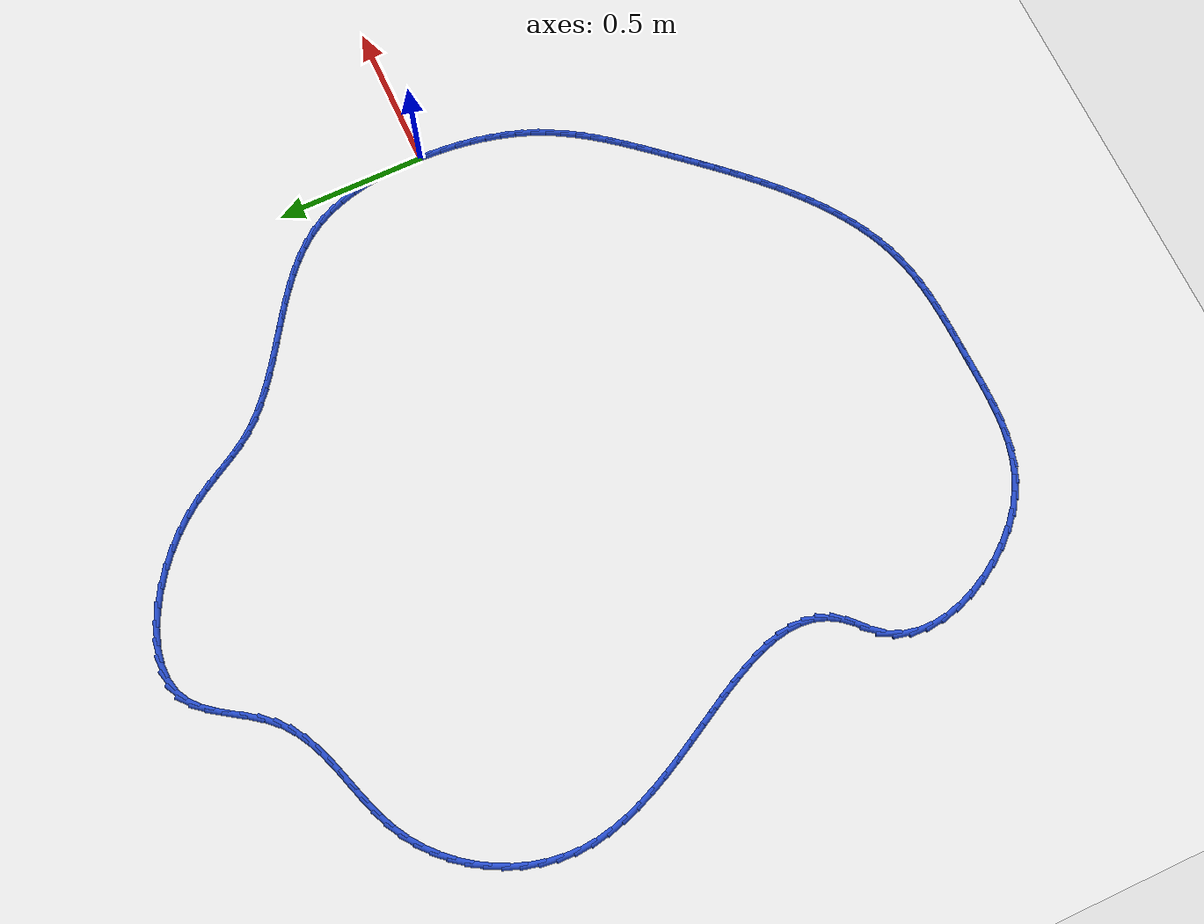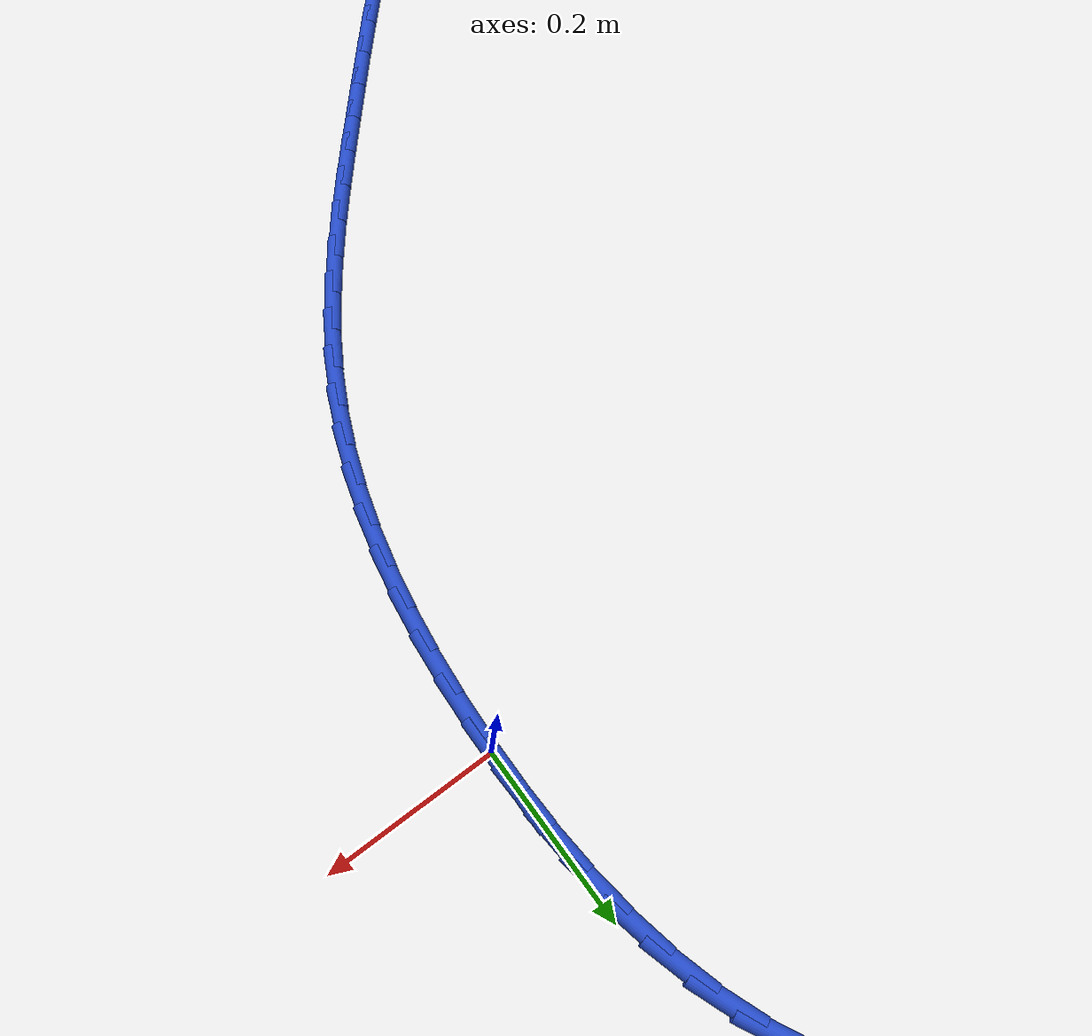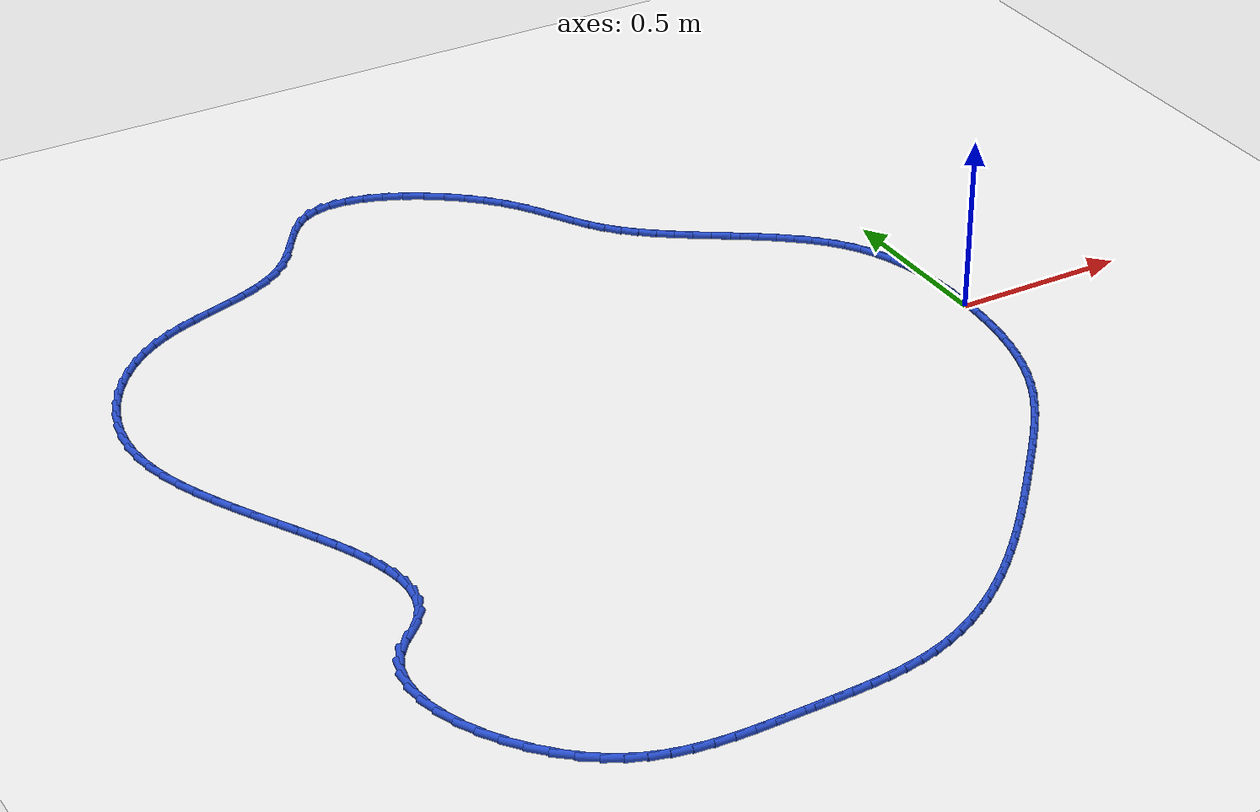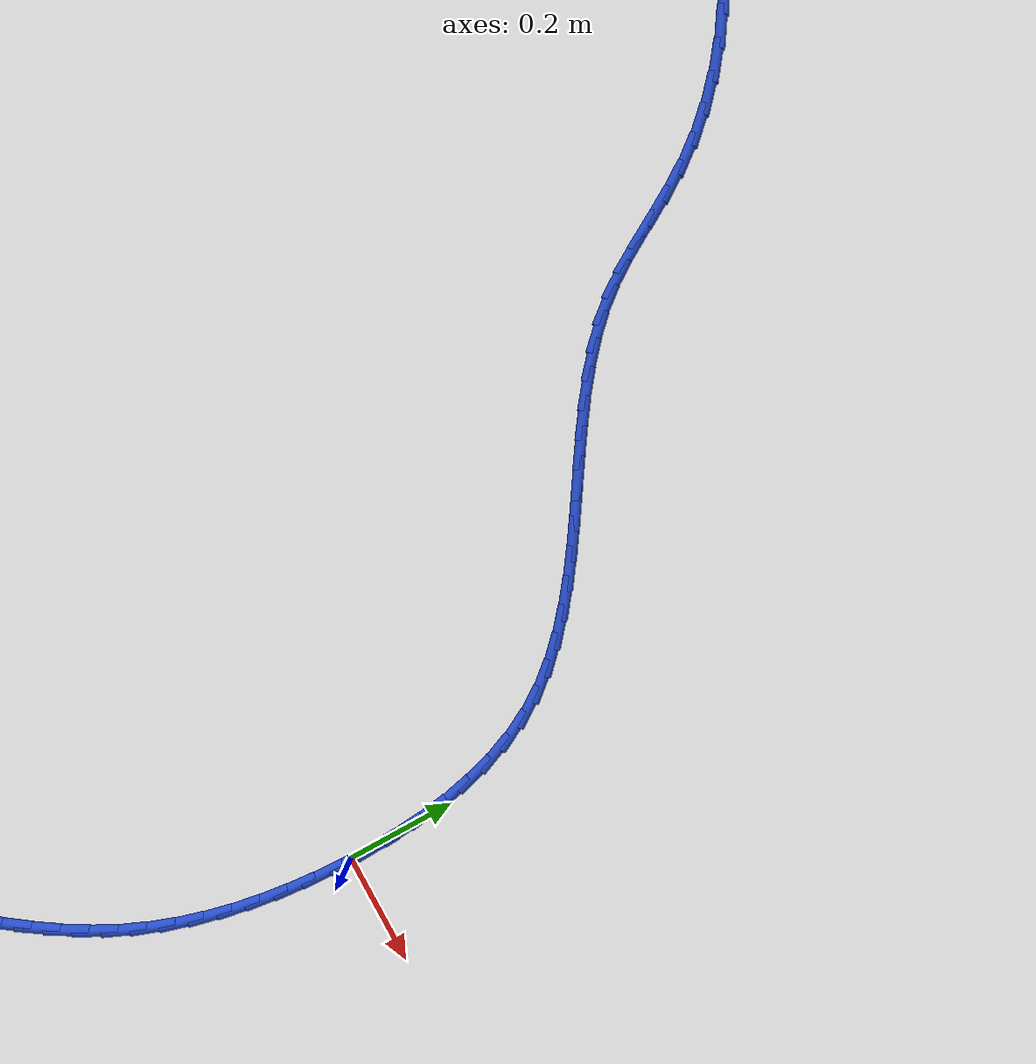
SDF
<sdf version="1.6">
 <world name="default">
  <light name="sun" type="directional">
   <pose>0 0 10 0 -0 0</pose>
   <diffuse>0.8 0.8 0.8 1</diffuse>
   <specular>0.2 0.2 0.2 1</specular>
   <attenuation>
    <range>1000</range>
    <constant>0.9</constant>
    <linear>0.01</linear>
    <quadratic>0.001</quadratic>
   </attenuation>
   <direction>-0.5 0.1 -0.9</direction>
  </light>
  <model name="ground_plane">
   <static>1</static>
   <link name="link">
    <collision name="collision">
     <geometry><plane><normal>0 0 1</normal><size>100 100</size></plane></geometry>
     <surface><friction><ode><mu>100</mu><mu2>50</mu2></ode></friction></surface>
    </collision>
    <visual name="visual">
     <cast_shadows>0</cast_shadows>
     <geometry><plane><normal>0 0 1</normal><size>100 100</size></plane></geometry>
     <material>
      <script><uri>file://media/materials/scripts/gazebo.material</uri><name>Gazebo/WhiteGlow</name></script>
     </material>
    </visual>
   </link>
  </model>
  <gravity>0 0 -9.8</gravity>
  <magnetic_field>6e-06 2.3e-05 -4.2e-05</magnetic_field>
  <atmosphere type="adiabatic"/>
  <physics name="default_physics" default="0" type="ode">
   <max_step_size>0.001</max_step_size>
   <real_time_factor>1</real_time_factor>
   <real_time_update_rate>1000</real_time_update_rate>
  </physics>
  <scene><ambient>0.4 0.4 0.4 1</ambient><background>0.7 0.7 0.7 1</background><shadows>1</shadows></scene>
  <spherical_coordinates>
   <surface_model>EARTH_WGS84</surface_model>
   <latitude_deg>0</latitude_deg>
   <longitude_deg>0</longitude_deg>
   <elevation>0</elevation>
   <heading_deg>0</heading_deg>
  </spherical_coordinates>
  <model name="line">
   <link name="link_0">
    <pose>-4.0766001685454967e-17 -4.163336342344337e-17 0.01 0 1.57 1.5677588996940441</pose>
    <collision name="collision">
     <geometry><cylinder><radius>0.01</radius><length>0.08</length></cylinder></geometry>
    </collision>
    <visual name="visual">
     <material>
      <script><name>Gazebo/Blue</name><uri>file://media/materials/scripts/gazebo.material</uri></script>
     </material>
     <geometry><cylinder><radius>0.01</radius><length>0.08</length></cylinder></geometry>
    </visual>
   </link>
   <link name="link_1">
    <pose>0.00016220308232994086 0.0534013091071658 0.01 0 1.57 -1.5304724078214895</pose>
    <collision name="collision">
     <geometry><cylinder><radius>0.01</radius><length>0.08</length></cylinder></geometry>
    </collision>
    <visual name="visual">
     <material>
      <script><name>Gazebo/Blue</name><uri>file://media/materials/scripts/gazebo.material</uri></script>
     </material>
     <geometry><cylinder><radius>0.01</radius><length>0.08</length></cylinder></geometry>
    </visual>
   </link>
   <link name="link_2">
    <pose>-0.0019910451538661202 0.10677114742330737 0.01 0 1.57 -1.4799756854001473</pose>
    <collision name="collision">
     <geometry><cylinder><radius>0.01</radius><length>0.08</length></cylinder></geometry>
    </collision>
    <visual name="visual">
     <material>
      <script><name>Gazebo/Blue</name><uri>file://media/materials/scripts/gazebo.material</uri></script>
     </material>
     <geometry><cylinder><radius>0.01</radius><length>0.08</length></cylinder></geometry>
    </visual>
   </link>
   <link name="link_3">
    <pose>-0.006807744157143915 0.1596605380490093 0.01 0 1.57 -1.4212635857250937</pose>
    <collision name="collision">
     <geometry><cylinder><radius>0.01</radius><length>0.08</length></cylinder></geometry>
    </collision>
    <visual name="visual">
     <material>
      <script><name>Gazebo/Blue</name><uri>file://media/materials/scripts/gazebo.material</uri></script>
     </material>
     <geometry><cylinder><radius>0.01</radius><length>0.08</length></cylinder></geometry>
    </visual>
   </link>
   <link name="link_4">
    <pose>-0.01463589337605914 0.21162050408485625 0.01 0 1.57 -1.3531213712180754</pose>
    <collision name="collision">
     <geometry><cylinder><radius>0.01</radius><length>0.08</length></cylinder></geometry>
    </collision>
    <visual name="visual">
     <material>
      <script><name>Gazebo/Blue</name><uri>file://media/materials/scripts/gazebo.material</uri></script>
     </material>
     <geometry><cylinder><radius>0.01</radius><length>0.08</length></cylinder></geometry>
    </visual>
   </link>
   <link name="link_5">
    <pose>-0.025823492259167476 0.26220206863143286 0.01 0 1.57 -1.2742892462462632</pose>
    <collision name="collision">
     <geometry><cylinder><radius>0.01</radius><length>0.08</length></cylinder></geometry>
    </collision>
    <visual name="visual">
     <material>
      <script><name>Gazebo/Blue</name><uri>file://media/materials/scripts/gazebo.material</uri></script>
     </material>
     <geometry><cylinder><radius>0.01</radius><length>0.08</length></cylinder></geometry>
    </visual>
   </link>
   <link name="link_6">
    <pose>-0.040718540255024624 0.3109562547893239 0.01 0 1.57 -1.1836422986486972</pose>
    <collision name="collision">
     <geometry><cylinder><radius>0.01</radius><length>0.08</length></cylinder></geometry>
    </collision>
    <visual name="visual">
     <material>
      <script><name>Gazebo/Blue</name><uri>file://media/materials/scripts/gazebo.material</uri></script>
     </material>
     <geometry><cylinder><radius>0.01</radius><length>0.08</length></cylinder></geometry>
    </visual>
   </link>
   <link name="link_7">
    <pose>-0.059669036812186264 0.35743408565911367 0.01 0 1.57 -1.0804960133434083</pose>
    <collision name="collision">
     <geometry><cylinder><radius>0.01</radius><length>0.08</length></cylinder></geometry>
    </collision>
    <visual name="visual">
     <material>
      <script><name>Gazebo/Blue</name><uri>file://media/materials/scripts/gazebo.material</uri></script>
     </material>
     <geometry><cylinder><radius>0.01</radius><length>0.08</length></cylinder></geometry>
    </visual>
   </link>
   <link name="link_8">
    <pose>-0.0830229813792081 0.40118658434138715 0.01 0 1.57 -0.9678921384574665</pose>
    <collision name="collision">
     <geometry><cylinder><radius>0.01</radius><length>0.08</length></cylinder></geometry>
    </collision>
    <visual name="visual">
     <material>
      <script><name>Gazebo/Blue</name><uri>file://media/materials/scripts/gazebo.material</uri></script>
     </material>
     <geometry><cylinder><radius>0.01</radius><length>0.08</length></cylinder></geometry>
    </visual>
   </link>
   <link name="link_9">
    <pose>-0.11102216219700192 0.4418589022264239 0.01 0 1.57 -0.8644142401468418</pose>
    <collision name="collision">
     <geometry><cylinder><radius>0.01</radius><length>0.08</length></cylinder></geometry>
    </collision>
    <visual name="visual">
     <material>
      <script><name>Gazebo/Blue</name><uri>file://media/materials/scripts/gazebo.material</uri></script>
     </material>
     <geometry><cylinder><radius>0.01</radius><length>0.08</length></cylinder></geometry>
    </visual>
   </link>
   <link name="link_10">
    <pose>-0.1432744859750789 0.479657959897639 0.01 0 1.57 -0.7778306572685271</pose>
    <collision name="collision">
     <geometry><cylinder><radius>0.01</radius><length>0.08</length></cylinder></geometry>
    </collision>
    <visual name="visual">
     <material>
      <script><name>Gazebo/Blue</name><uri>file://media/materials/scripts/gazebo.material</uri></script>
     </material>
     <geometry><cylinder><radius>0.01</radius><length>0.08</length></cylinder></geometry>
    </visual>
   </link>
   <link name="link_11">
    <pose>-0.17915369398899497 0.5149982039829473 0.01 0 1.57 -0.7081954984737049</pose>
    <collision name="collision">
     <geometry><cylinder><radius>0.01</radius><length>0.08</length></cylinder></geometry>
    </collision>
    <visual name="visual">
     <material>
      <script><name>Gazebo/Blue</name><uri>file://media/materials/scripts/gazebo.material</uri></script>
     </material>
     <geometry><cylinder><radius>0.01</radius><length>0.08</length></cylinder></geometry>
    </visual>
   </link>
   <link name="link_12">
    <pose>-0.218033153467153 0.5482944126046474 0.01 0 1.57 -0.6546868858009461</pose>
    <collision name="collision">
     <geometry><cylinder><radius>0.01</radius><length>0.08</length></cylinder></geometry>
    </collision>
    <visual name="visual">
     <material>
      <script><name>Gazebo/Blue</name><uri>file://media/materials/scripts/gazebo.material</uri></script>
     </material>
     <geometry><cylinder><radius>0.01</radius><length>0.08</length></cylinder></geometry>
    </visual>
   </link>
   <link name="link_13">
    <pose>-0.25928623163795567 0.5799613638850376 0.01 0 1.57 -0.6162054611898571</pose>
    <collision name="collision">
     <geometry><cylinder><radius>0.01</radius><length>0.08</length></cylinder></geometry>
    </collision>
    <visual name="visual">
     <material>
      <script><name>Gazebo/Blue</name><uri>file://media/materials/scripts/gazebo.material</uri></script>
     </material>
     <geometry><cylinder><radius>0.01</radius><length>0.08</length></cylinder></geometry>
    </visual>
   </link>
   <link name="link_14">
    <pose>-0.3022862957298058 0.6104138359464166 0.01 0 1.57 -0.591745949207315</pose>
    <collision name="collision">
     <geometry><cylinder><radius>0.01</radius><length>0.08</length></cylinder></geometry>
    </collision>
    <visual name="visual">
     <material>
      <script><name>Gazebo/Blue</name><uri>file://media/materials/scripts/gazebo.material</uri></script>
     </material>
     <geometry><cylinder><radius>0.01</radius><length>0.08</length></cylinder></geometry>
    </visual>
   </link>
   <link name="link_15">
    <pose>-0.34640671297110626 0.6400666069110827 0.01 0 1.57 -0.5805968481344407</pose>
    <collision name="collision">
     <geometry><cylinder><radius>0.01</radius><length>0.08</length></cylinder></geometry>
    </collision>
    <visual name="visual">
     <material>
      <script><name>Gazebo/Blue</name><uri>file://media/materials/scripts/gazebo.material</uri></script>
     </material>
     <geometry><cylinder><radius>0.01</radius><length>0.08</length></cylinder></geometry>
    </visual>
   </link>
   <link name="link_16">
    <pose>-0.39102085059025976 0.6693344549013343 0.01 0 1.57 -0.5824343099816993</pose>
    <collision name="collision">
     <geometry><cylinder><radius>0.01</radius><length>0.08</length></cylinder></geometry>
    </collision>
    <visual name="visual">
     <material>
      <script><name>Gazebo/Blue</name><uri>file://media/materials/scripts/gazebo.material</uri></script>
     </material>
     <geometry><cylinder><radius>0.01</radius><length>0.08</length></cylinder></geometry>
    </visual>
   </link>
   <link name="link_17">
    <pose>-0.4355020758156693 0.6986321580394699 0.01 0 1.57 -0.5973579654824207</pose>
    <collision name="collision">
     <geometry><cylinder><radius>0.01</radius><length>0.08</length></cylinder></geometry>
    </collision>
    <visual name="visual">
     <material>
      <script><name>Gazebo/Blue</name><uri>file://media/materials/scripts/gazebo.material</uri></script>
     </material>
     <geometry><cylinder><radius>0.01</radius><length>0.08</length></cylinder></geometry>
    </visual>
   </link>
   <link name="link_18">
    <pose>-0.47922375587573746 0.7283744944477879 0.01 0 1.57 -0.625890202995978</pose>
    <collision name="collision">
     <geometry><cylinder><radius>0.01</radius><length>0.08</length></cylinder></geometry>
    </collision>
    <visual name="visual">
     <material>
      <script><name>Gazebo/Blue</name><uri>file://media/materials/scripts/gazebo.material</uri></script>
     </material>
     <geometry><cylinder><radius>0.01</radius><length>0.08</length></cylinder></geometry>
    </visual>
   </link>
   <link name="link_19">
    <pose>-0.521559257998867 0.7589762422485866 0.01 0 1.57 -0.6689343251122071</pose>
    <collision name="collision">
     <geometry><cylinder><radius>0.01</radius><length>0.08</length></cylinder></geometry>
    </collision>
    <visual name="visual">
     <material>
      <script><name>Gazebo/Blue</name><uri>file://media/materials/scripts/gazebo.material</uri></script>
     </material>
     <geometry><cylinder><radius>0.01</radius><length>0.08</length></cylinder></geometry>
    </visual>
   </link>
   <link name="link_20">
    <pose>-0.5618819494134609 0.7908521795641648 0.01 0 1.57 -0.7276596073566541</pose>
    <collision name="collision">
     <geometry><cylinder><radius>0.01</radius><length>0.08</length></cylinder></geometry>
    </collision>
    <visual name="visual">
     <material>
      <script><name>Gazebo/Blue</name><uri>file://media/materials/scripts/gazebo.material</uri></script>
     </material>
     <geometry><cylinder><radius>0.01</radius><length>0.08</length></cylinder></geometry>
    </visual>
   </link>
   <link name="link_21">
    <pose>-0.599565197347922 0.8244170845168208 0.01 0 1.57 -0.8032526452384804</pose>
    <collision name="collision">
     <geometry><cylinder><radius>0.01</radius><length>0.08</length></cylinder></geometry>
    </collision>
    <visual name="visual">
     <material>
      <script><name>Gazebo/Blue</name><uri>file://media/materials/scripts/gazebo.material</uri></script>
     </material>
     <geometry><cylinder><radius>0.01</radius><length>0.08</length></cylinder></geometry>
    </visual>
   </link>
   <link name="link_22">
    <pose>-0.6339823690306529 0.8600857352288527 0.01 0 1.57 -0.8958804146261714</pose>
    <collision name="collision">
     <geometry><cylinder><radius>0.01</radius><length>0.08</length></cylinder></geometry>
    </collision>
    <visual name="visual">
     <material>
      <script><name>Gazebo/Blue</name><uri>file://media/materials/scripts/gazebo.material</uri></script>
     </material>
     <geometry><cylinder><radius>0.01</radius><length>0.08</length></cylinder></geometry>
    </visual>
   </link>
   <link name="link_23">
    <pose>-0.6645336790737719 0.8982611777777064 0.01 0 1.57 -0.9832128160586784</pose>
    <collision name="collision">
     <geometry><cylinder><radius>0.01</radius><length>0.08</length></cylinder></geometry>
    </collision>
    <visual name="visual">
     <material>
      <script><name>Gazebo/Blue</name><uri>file://media/materials/scripts/gazebo.material</uri></script>
     </material>
     <geometry><cylinder><radius>0.01</radius><length>0.08</length></cylinder></geometry>
    </visual>
   </link>
   <link name="link_24">
    <pose>-0.6916105100621098 0.9389133275031689 0.01 0 1.57 -1.0351899689098694</pose>
    <collision name="collision">
     <geometry><cylinder><radius>0.01</radius><length>0.08</length></cylinder></geometry>
    </collision>
    <visual name="visual">
     <material>
      <script><name>Gazebo/Blue</name><uri>file://media/materials/scripts/gazebo.material</uri></script>
     </material>
     <geometry><cylinder><radius>0.01</radius><length>0.08</length></cylinder></geometry>
    </visual>
   </link>
   <link name="link_25">
    <pose>-0.7168622190427819 0.9814623771734721 0.01 0 1.57 -1.0497431225457825</pose>
    <collision name="collision">
     <geometry><cylinder><radius>0.01</radius><length>0.08</length></cylinder></geometry>
    </collision>
    <visual name="visual">
     <material>
      <script><name>Gazebo/Blue</name><uri>file://media/materials/scripts/gazebo.material</uri></script>
     </material>
     <geometry><cylinder><radius>0.01</radius><length>0.08</length></cylinder></geometry>
    </visual>
   </link>
   <link name="link_26">
    <pose>-0.7420193240437293 1.0252930529997522 0.01 0 1.57 -1.0288117347057388</pose>
    <collision name="collision">
     <geometry><cylinder><radius>0.01</radius><length>0.08</length></cylinder></geometry>
    </collision>
    <visual name="visual">
     <material>
      <script><name>Gazebo/Blue</name><uri>file://media/materials/scripts/gazebo.material</uri></script>
     </material>
     <geometry><cylinder><radius>0.01</radius><length>0.08</length></cylinder></geometry>
    </visual>
   </link>
   <link name="link_27">
    <pose>-0.768812343092894 1.069790081193147 0.01 0 1.57 -0.9756680608584856</pose>
    <collision name="collision">
     <geometry><cylinder><radius>0.01</radius><length>0.08</length></cylinder></geometry>
    </collision>
    <visual name="visual">
     <material>
      <script><name>Gazebo/Blue</name><uri>file://media/materials/scripts/gazebo.material</uri></script>
     </material>
     <geometry><cylinder><radius>0.01</radius><length>0.08</length></cylinder></geometry>
    </visual>
   </link>
   <link name="link_28">
    <pose>-0.7989717942182168 1.1143381879647911 0.01 0 1.57 -0.8957525189096694</pose>
    <collision name="collision">
     <geometry><cylinder><radius>0.01</radius><length>0.08</length></cylinder></geometry>
    </collision>
    <visual name="visual">
     <material>
      <script><name>Gazebo/Blue</name><uri>file://media/materials/scripts/gazebo.material</uri></script>
     </material>
     <geometry><cylinder><radius>0.01</radius><length>0.08</length></cylinder></geometry>
    </visual>
   </link>
   <link name="link_29">
    <pose>-0.8341761237198331 1.1583162883378422 0.01 0 1.57 -0.8094557008551096</pose>
    <collision name="collision">
     <geometry><cylinder><radius>0.01</radius><length>0.08</length></cylinder></geometry>
    </collision>
    <visual name="visual">
     <material>
      <script><name>Gazebo/Blue</name><uri>file://media/materials/scripts/gazebo.material</uri></script>
     </material>
     <geometry><cylinder><radius>0.01</radius><length>0.08</length></cylinder></geometry>
    </visual>
   </link>
   <link name="link_30">
    <pose>-0.874815390832017 1.200959513755599 0.01 0 1.57 -0.7301495612855831</pose>
    <collision name="collision">
     <geometry><cylinder><radius>0.01</radius><length>0.08</length></cylinder></geometry>
    </collision>
    <visual name="visual">
     <material>
      <script><name>Gazebo/Blue</name><uri>file://media/materials/scripts/gazebo.material</uri></script>
     </material>
     <geometry><cylinder><radius>0.01</radius><length>0.08</length></cylinder></geometry>
    </visual>
   </link>
   <link name="link_31">
    <pose>-0.9199387462291341 1.2413533506997603 0.01 0 1.57 -0.6536618966945924</pose>
    <collision name="collision">
     <geometry><cylinder><radius>0.01</radius><length>0.08</length></cylinder></geometry>
    </collision>
    <visual name="visual">
     <material>
      <script><name>Gazebo/Blue</name><uri>file://media/materials/scripts/gazebo.material</uri></script>
     </material>
     <geometry><cylinder><radius>0.01</radius><length>0.08</length></cylinder></geometry>
    </visual>
   </link>
   <link name="link_32">
    <pose>-0.9685327593015145 1.2785763016009646 0.01 0 1.57 -0.5756486519359343</pose>
    <collision name="collision">
     <geometry><cylinder><radius>0.01</radius><length>0.08</length></cylinder></geometry>
    </collision>
    <visual name="visual">
     <material>
      <script><name>Gazebo/Blue</name><uri>file://media/materials/scripts/gazebo.material</uri></script>
     </material>
     <geometry><cylinder><radius>0.01</radius><length>0.08</length></cylinder></geometry>
    </visual>
   </link>
   <link name="link_33">
    <pose>-1.019583999439489 1.311706868889852 0.01 0 1.57 -0.49172547068154077</pose>
    <collision name="collision">
     <geometry><cylinder><radius>0.01</radius><length>0.08</length></cylinder></geometry>
    </collision>
    <visual name="visual">
     <material>
      <script><name>Gazebo/Blue</name><uri>file://media/materials/scripts/gazebo.material</uri></script>
     </material>
     <geometry><cylinder><radius>0.01</radius><length>0.08</length></cylinder></geometry>
    </visual>
   </link>
   <link name="link_34">
    <pose>-1.0720790360333885 1.3398235549970618 0.01 0 1.57 -0.39686705837718605</pose>
    <collision name="collision">
     <geometry><cylinder><radius>0.01</radius><length>0.08</length></cylinder></geometry>
    </collision>
    <visual name="visual">
     <material>
      <script><name>Gazebo/Blue</name><uri>file://media/materials/scripts/gazebo.material</uri></script>
     </material>
     <geometry><cylinder><radius>0.01</radius><length>0.08</length></cylinder></geometry>
    </visual>
   </link>
   <link name="link_35">
    <pose>-1.125004438473543 1.362004862353234 0.01 0 1.57 -0.2848135399150614</pose>
    <collision name="collision">
     <geometry><cylinder><radius>0.01</radius><length>0.08</length></cylinder></geometry>
    </collision>
    <visual name="visual">
     <material>
      <script><name>Gazebo/Blue</name><uri>file://media/materials/scripts/gazebo.material</uri></script>
     </material>
     <geometry><cylinder><radius>0.01</radius><length>0.08</length></cylinder></geometry>
    </visual>
   </link>
   <link name="link_36">
    <pose>-1.177346776150283 1.3773292933890078 0.01 0 1.57 -0.14762121172356363</pose>
    <collision name="collision">
     <geometry><cylinder><radius>0.01</radius><length>0.08</length></cylinder></geometry>
    </collision>
    <visual name="visual">
     <material>
      <script><name>Gazebo/Blue</name><uri>file://media/materials/scripts/gazebo.material</uri></script>
     </material>
     <geometry><cylinder><radius>0.01</radius><length>0.08</length></cylinder></geometry>
    </visual>
   </link>
   <link name="link_37">
    <pose>-1.228092618453939 1.3848753505350226 0.01 0 1.57 0.02396533607206576</pose>
    <collision name="collision">
     <geometry><cylinder><radius>0.01</radius><length>0.08</length></cylinder></geometry>
    </collision>
    <visual name="visual">
     <material>
      <script><name>Gazebo/Blue</name><uri>file://media/materials/scripts/gazebo.material</uri></script>
     </material>
     <geometry><cylinder><radius>0.01</radius><length>0.08</length></cylinder></geometry>
    </visual>
   </link>
   <link name="link_38">
    <pose>-1.276228534774842 1.3837215362219186 0.01 0 1.57 0.2375019153599429</pose>
    <collision name="collision">
     <geometry><cylinder><radius>0.01</radius><length>0.08</length></cylinder></geometry>
    </collision>
    <visual name="visual">
     <material>
      <script><name>Gazebo/Blue</name><uri>file://media/materials/scripts/gazebo.material</uri></script>
     </material>
     <geometry><cylinder><radius>0.01</radius><length>0.08</length></cylinder></geometry>
    </visual>
   </link>
   <link name="link_39">
    <pose>-1.3207410945033216 1.3729463528803345 0.01 0 1.57 0.49093916707123003</pose>
    <collision name="collision">
     <geometry><cylinder><radius>0.01</radius><length>0.08</length></cylinder></geometry>
    </collision>
    <visual name="visual">
     <material>
      <script><name>Gazebo/Blue</name><uri>file://media/materials/scripts/gazebo.material</uri></script>
     </material>
     <geometry><cylinder><radius>0.01</radius><length>0.08</length></cylinder></geometry>
    </visual>
   </link>
   <link name="link_40">
    <pose>-1.3606171894450843 1.3516287873410493 0.01 0 1.57 0.7406119326496913</pose>
    <collision name="collision">
     <geometry><cylinder><radius>0.01</radius><length>0.08</length></cylinder></geometry>
    </collision>
    <visual name="visual">
     <material>
      <script><name>Gazebo/Blue</name><uri>file://media/materials/scripts/gazebo.material</uri></script>
     </material>
     <geometry><cylinder><radius>0.01</radius><length>0.08</length></cylinder></geometry>
    </visual>
   </link>
   <link name="link_41">
    <pose>-1.3954605451085118 1.3197745636636793 0.01 0 1.57 0.9008215098158752</pose>
    <collision name="collision">
     <geometry><cylinder><radius>0.01</radius><length>0.08</length></cylinder></geometry>
    </collision>
    <visual name="visual">
     <material>
      <script><name>Gazebo/Blue</name><uri>file://media/materials/scripts/gazebo.material</uri></script>
     </material>
     <geometry><cylinder><radius>0.01</radius><length>0.08</length></cylinder></geometry>
    </visual>
   </link>
   <link name="link_42">
    <pose>-1.426775938758928 1.2802455654034435 0.01 0 1.57 0.9755309504757887</pose>
    <collision name="collision">
     <geometry><cylinder><radius>0.01</radius><length>0.08</length></cylinder></geometry>
    </collision>
    <visual name="visual">
     <material>
      <script><name>Gazebo/Blue</name><uri>file://media/materials/scripts/gazebo.material</uri></script>
     </material>
     <geometry><cylinder><radius>0.01</radius><length>0.08</length></cylinder></geometry>
    </visual>
   </link>
   <link name="link_43">
    <pose>-1.456433212555893 1.236452153325807 0.01 0 1.57 0.9811825235593502</pose>
    <collision name="collision">
     <geometry><cylinder><radius>0.01</radius><length>0.08</length></cylinder></geometry>
    </collision>
    <visual name="visual">
     <material>
      <script><name>Gazebo/Blue</name><uri>file://media/materials/scripts/gazebo.material</uri></script>
     </material>
     <geometry><cylinder><radius>0.01</radius><length>0.08</length></cylinder></geometry>
    </visual>
   </link>
   <link name="link_44">
    <pose>-1.486302208658969 1.1918046881962385 0.01 0 1.57 0.921509227882303</pose>
    <collision name="collision">
     <geometry><cylinder><radius>0.01</radius><length>0.08</length></cylinder></geometry>
    </collision>
    <visual name="visual">
     <material>
      <script><name>Gazebo/Blue</name><uri>file://media/materials/scripts/gazebo.material</uri></script>
     </material>
     <geometry><cylinder><radius>0.01</radius><length>0.08</length></cylinder></geometry>
    </visual>
   </link>
   <link name="link_45">
    <pose>-1.5182527692277161 1.1497135307802022 0.01 0 1.57 0.7921929371656502</pose>
    <collision name="collision">
     <geometry><cylinder><radius>0.01</radius><length>0.08</length></cylinder></geometry>
    </collision>
    <visual name="visual">
     <material>
      <script><name>Gazebo/Blue</name><uri>file://media/materials/scripts/gazebo.material</uri></script>
     </material>
     <geometry><cylinder><radius>0.01</radius><length>0.08</length></cylinder></geometry>
    </visual>
   </link>
   <link name="link_46">
    <pose>-1.554058874998976 1.1134174997614488 0.01 0 1.57 0.6398658212087711</pose>
    <collision name="collision">
     <geometry><cylinder><radius>0.01</radius><length>0.08</length></cylinder></geometry>
    </collision>
    <visual name="visual">
     <material>
      <script><name>Gazebo/Blue</name><uri>file://media/materials/scripts/gazebo.material</uri></script>
     </material>
     <geometry><cylinder><radius>0.01</radius><length>0.08</length></cylinder></geometry>
    </visual>
   </link>
   <link name="link_47">
    <pose>-1.594081650379193 1.0836271359282754 0.01 0 1.57 0.512716814159115</pose>
    <collision name="collision">
     <geometry><cylinder><radius>0.01</radius><length>0.08</length></cylinder></geometry>
    </collision>
    <visual name="visual">
     <material>
      <script><name>Gazebo/Blue</name><uri>file://media/materials/scripts/gazebo.material</uri></script>
     </material>
     <geometry><cylinder><radius>0.01</radius><length>0.08</length></cylinder></geometry>
    </visual>
   </link>
   <link name="link_48">
    <pose>-1.6376054998058849 1.0591262114100246 0.01 0 1.57 0.41653196900353706</pose>
    <collision name="collision">
     <geometry><cylinder><radius>0.01</radius><length>0.08</length></cylinder></geometry>
    </collision>
    <visual name="visual">
     <material>
      <script><name>Gazebo/Blue</name><uri>file://media/materials/scripts/gazebo.material</uri></script>
     </material>
     <geometry><cylinder><radius>0.01</radius><length>0.08</length></cylinder></geometry>
    </visual>
   </link>
   <link name="link_49">
    <pose>-1.6838877530583984 1.038650048781536 0.01 0 1.57 0.35156919322046076</pose>
    <collision name="collision">
     <geometry><cylinder><radius>0.01</radius><length>0.08</length></cylinder></geometry>
    </collision>
    <visual name="visual">
     <material>
      <script><name>Gazebo/Blue</name><uri>file://media/materials/scripts/gazebo.material</uri></script>
     </material>
     <geometry><cylinder><radius>0.01</radius><length>0.08</length></cylinder></geometry>
    </visual>
   </link>
   <link name="link_50">
    <pose>-1.7321857399160803 1.020933970617649 0.01 0 1.57 0.3162390852858655</pose>
    <collision name="collision">
     <geometry><cylinder><radius>0.01</radius><length>0.08</length></cylinder></geometry>
    </collision>
    <visual name="visual">
     <material>
      <script><name>Gazebo/Blue</name><uri>file://media/materials/scripts/gazebo.material</uri></script>
     </material>
     <geometry><cylinder><radius>0.01</radius><length>0.08</length></cylinder></geometry>
    </visual>
   </link>
   <link name="link_51">
    <pose>-1.7817567901582767 1.0047132994932044 0.01 0 1.57 0.3089329021948328</pose>
    <collision name="collision">
     <geometry><cylinder><radius>0.01</radius><length>0.08</length></cylinder></geometry>
    </collision>
    <visual name="visual">
     <material>
      <script><name>Gazebo/Blue</name><uri>file://media/materials/scripts/gazebo.material</uri></script>
     </material>
     <geometry><cylinder><radius>0.01</radius><length>0.08</length></cylinder></geometry>
    </visual>
   </link>
   <link name="link_52">
    <pose>-1.831858233564334 0.9887233579830418 0.01 0 1.57 0.3288443928358384</pose>
    <collision name="collision">
     <geometry><cylinder><radius>0.01</radius><length>0.08</length></cylinder></geometry>
    </collision>
    <visual name="visual">
     <material>
      <script><name>Gazebo/Blue</name><uri>file://media/materials/scripts/gazebo.material</uri></script>
     </material>
     <geometry><cylinder><radius>0.01</radius><length>0.08</length></cylinder></geometry>
    </visual>
   </link>
   <link name="link_53">
    <pose>-1.8817473999135994 0.9716994686620011 0.01 0 1.57 0.37607367094317373</pose>
    <collision name="collision">
     <geometry><cylinder><radius>0.01</radius><length>0.08</length></cylinder></geometry>
    </collision>
    <visual name="visual">
     <material>
      <script><name>Gazebo/Blue</name><uri>file://media/materials/scripts/gazebo.material</uri></script>
     </material>
     <geometry><cylinder><radius>0.01</radius><length>0.08</length></cylinder></geometry>
    </visual>
   </link>
   <link name="link_54">
    <pose>-1.9306816189854195 0.9523769541049222 0.01 0 1.57 0.4511654746971185</pose>
    <collision name="collision">
     <geometry><cylinder><radius>0.01</radius><length>0.08</length></cylinder></geometry>
    </collision>
    <visual name="visual">
     <material>
      <script><name>Gazebo/Blue</name><uri>file://media/materials/scripts/gazebo.material</uri></script>
     </material>
     <geometry><cylinder><radius>0.01</radius><length>0.08</length></cylinder></geometry>
    </visual>
   </link>
   <link name="link_55">
    <pose>-1.97791822055914 0.9294911368866452 0.01 0 1.57 0.55095496396628</pose>
    <collision name="collision">
     <geometry><cylinder><radius>0.01</radius><length>0.08</length></cylinder></geometry>
    </collision>
    <visual name="visual">
     <material>
      <script><name>Gazebo/Blue</name><uri>file://media/materials/scripts/gazebo.material</uri></script>
     </material>
     <geometry><cylinder><radius>0.01</radius><length>0.08</length></cylinder></geometry>
    </visual>
   </link>
   <link name="link_56">
    <pose>-2.022753228169089 0.9019436152568371 0.01 0 1.57 0.6545374058064372</pose>
    <collision name="collision">
     <geometry><cylinder><radius>0.01</radius><length>0.08</length></cylinder></geometry>
    </collision>
    <visual name="visual">
     <material>
      <script><name>Gazebo/Blue</name><uri>file://media/materials/scripts/gazebo.material</uri></script>
     </material>
     <geometry><cylinder><radius>0.01</radius><length>0.08</length></cylinder></geometry>
    </visual>
   </link>
   <link name="link_57">
    <pose>-2.064736371474297 0.8697262191346495 0.01 0 1.57 0.7544801730021004</pose>
    <collision name="collision">
     <geometry><cylinder><radius>0.01</radius><length>0.08</length></cylinder></geometry>
    </collision>
    <visual name="visual">
     <material>
      <script><name>Gazebo/Blue</name><uri>file://media/materials/scripts/gazebo.material</uri></script>
     </material>
     <geometry><cylinder><radius>0.01</radius><length>0.08</length></cylinder></geometry>
    </visual>
   </link>
   <link name="link_58">
    <pose>-2.103519589529325 0.8332699949542457 0.01 0 1.57 0.8518880456477844</pose>
    <collision name="collision">
     <geometry><cylinder><radius>0.01</radius><length>0.08</length></cylinder></geometry>
    </collision>
    <visual name="visual">
     <material>
      <script><name>Gazebo/Blue</name><uri>file://media/materials/scripts/gazebo.material</uri></script>
     </material>
     <geometry><cylinder><radius>0.01</radius><length>0.08</length></cylinder></geometry>
    </visual>
   </link>
   <link name="link_59">
    <pose>-2.1387551025939016 0.793007197550972 0.01 0 1.57 0.9479619852513224</pose>
    <collision name="collision">
     <geometry><cylinder><radius>0.01</radius><length>0.08</length></cylinder></geometry>
    </collision>
    <visual name="visual">
     <material>
      <script><name>Gazebo/Blue</name><uri>file://media/materials/scripts/gazebo.material</uri></script>
     </material>
     <geometry><cylinder><radius>0.01</radius><length>0.08</length></cylinder></geometry>
    </visual>
   </link>
   <link name="link_60">
    <pose>-2.17009513092776 0.7493700817601747 0.01 0 1.57 1.043914846331548</pose>
    <collision name="collision">
     <geometry><cylinder><radius>0.01</radius><length>0.08</length></cylinder></geometry>
    </collision>
    <visual name="visual">
     <material>
      <script><name>Gazebo/Blue</name><uri>file://media/materials/scripts/gazebo.material</uri></script>
     </material>
     <geometry><cylinder><radius>0.01</radius><length>0.08</length></cylinder></geometry>
    </visual>
   </link>
   <link name="link_61">
    <pose>-2.1971918947906293 0.7027909024171997 0.01 0 1.57 1.140922942183426</pose>
    <collision name="collision">
     <geometry><cylinder><radius>0.01</radius><length>0.08</length></cylinder></geometry>
    </collision>
    <visual name="visual">
     <material>
      <script><name>Gazebo/Blue</name><uri>file://media/materials/scripts/gazebo.material</uri></script>
     </material>
     <geometry><cylinder><radius>0.01</radius><length>0.08</length></cylinder></geometry>
    </visual>
   </link>
   <link name="link_62">
    <pose>-2.2196976144422416 0.6537019143573927 0.01 0 1.57 1.2400778924280236</pose>
    <collision name="collision">
     <geometry><cylinder><radius>0.01</radius><length>0.08</length></cylinder></geometry>
    </collision>
    <visual name="visual">
     <material>
      <script><name>Gazebo/Blue</name><uri>file://media/materials/scripts/gazebo.material</uri></script>
     </material>
     <geometry><cylinder><radius>0.01</radius><length>0.08</length></cylinder></geometry>
    </visual>
   </link>
   <link name="link_63">
    <pose>-2.237264510142325 0.6025353724161009 0.01 0 1.57 1.3423271985468213</pose>
    <collision name="collision">
     <geometry><cylinder><radius>0.01</radius><length>0.08</length></cylinder></geometry>
    </collision>
    <visual name="visual">
     <material>
      <script><name>Gazebo/Blue</name><uri>file://media/materials/scripts/gazebo.material</uri></script>
     </material>
     <geometry><cylinder><radius>0.01</radius><length>0.08</length></cylinder></geometry>
    </visual>
   </link>
   <link name="link_64">
    <pose>-2.249544802150613 0.5497235314286699 0.01 0 1.57 1.4483955883428854</pose>
    <collision name="collision">
     <geometry><cylinder><radius>0.01</radius><length>0.08</length></cylinder></geometry>
    </collision>
    <visual name="visual">
     <material>
      <script><name>Gazebo/Blue</name><uri>file://media/materials/scripts/gazebo.material</uri></script>
     </material>
     <geometry><cylinder><radius>0.01</radius><length>0.08</length></cylinder></geometry>
    </visual>
   </link>
   <link name="link_65">
    <pose>-2.256190710726834 0.49569864623044635 0.01 0 1.57 1.5586860305419754</pose>
    <collision name="collision">
     <geometry><cylinder><radius>0.01</radius><length>0.08</length></cylinder></geometry>
    </collision>
    <visual name="visual">
     <material>
      <script><name>Gazebo/Blue</name><uri>file://media/materials/scripts/gazebo.material</uri></script>
     </material>
     <geometry><cylinder><radius>0.01</radius><length>0.08</length></cylinder></geometry>
    </visual>
   </link>
   <link name="link_66">
    <pose>-2.2568544561307196 0.44089297165677593 0.01 0 1.57 -1.4698549438892863</pose>
    <collision name="collision">
     <geometry><cylinder><radius>0.01</radius><length>0.08</length></cylinder></geometry>
    </collision>
    <visual name="visual">
     <material>
      <script><name>Gazebo/Blue</name><uri>file://media/materials/scripts/gazebo.material</uri></script>
     </material>
     <geometry><cylinder><radius>0.01</radius><length>0.08</length></cylinder></geometry>
    </visual>
   </link>
   <link name="link_67">
    <pose>-2.2512659830111943 0.3857175873614582 0.01 0 1.57 -1.3674488302272605</pose>
    <collision name="collision">
     <geometry><cylinder><radius>0.01</radius><length>0.08</length></cylinder></geometry>
    </collision>
    <visual name="visual">
     <material>
      <script><name>Gazebo/Blue</name><uri>file://media/materials/scripts/gazebo.material</uri></script>
     </material>
     <geometry><cylinder><radius>0.01</radius><length>0.08</length></cylinder></geometry>
    </visual>
   </link>
   <link name="link_68">
    <pose>-2.239858009795903 0.33039210977156397 0.01 0 1.57 -1.2824223929628582</pose>
    <collision name="collision">
     <geometry><cylinder><radius>0.01</radius><length>0.08</length></cylinder></geometry>
    </collision>
    <visual name="visual">
     <material>
      <script><name>Gazebo/Blue</name><uri>file://media/materials/scripts/gazebo.material</uri></script>
     </material>
     <geometry><cylinder><radius>0.01</radius><length>0.08</length></cylinder></geometry>
    </visual>
   </link>
   <link name="link_69">
    <pose>-2.2234365605597857 0.2750344521687827 0.01 0 1.57 -1.2136423868926478</pose>
    <collision name="collision">
     <geometry><cylinder><radius>0.01</radius><length>0.08</length></cylinder></geometry>
    </collision>
    <visual name="visual">
     <material>
      <script><name>Gazebo/Blue</name><uri>file://media/materials/scripts/gazebo.material</uri></script>
     </material>
     <geometry><cylinder><radius>0.01</radius><length>0.08</length></cylinder></geometry>
    </visual>
   </link>
   <link name="link_70">
    <pose>-2.202811103179798 0.21976158960764275 0.01 0 1.57 -1.1595082617390093</pose>
    <collision name="collision">
     <geometry><cylinder><radius>0.01</radius><length>0.08</length></cylinder></geometry>
    </collision>
    <visual name="visual">
     <material>
      <script><name>Gazebo/Blue</name><uri>file://media/materials/scripts/gazebo.material</uri></script>
     </material>
     <geometry><cylinder><radius>0.01</radius><length>0.08</length></cylinder></geometry>
    </visual>
   </link>
   <link name="link_71">
    <pose>-2.1787911055329037 0.16469049714267245 0.01 0 1.57 -1.1184788472070968</pose>
    <collision name="collision">
     <geometry><cylinder><radius>0.01</radius><length>0.08</length></cylinder></geometry>
    </collision>
    <visual name="visual">
     <material>
      <script><name>Gazebo/Blue</name><uri>file://media/materials/scripts/gazebo.material</uri></script>
     </material>
     <geometry><cylinder><radius>0.01</radius><length>0.08</length></cylinder></geometry>
    </visual>
   </link>
   <link name="link_72">
    <pose>-2.1521860354960616 0.10993814982840097 0.01 0 1.57 -1.0893077389851333</pose>
    <collision name="collision">
     <geometry><cylinder><radius>0.01</radius><length>0.08</length></cylinder></geometry>
    </collision>
    <visual name="visual">
     <material>
      <script><name>Gazebo/Blue</name><uri>file://media/materials/scripts/gazebo.material</uri></script>
     </material>
     <geometry><cylinder><radius>0.01</radius><length>0.08</length></cylinder></geometry>
    </visual>
   </link>
   <link name="link_73">
    <pose>-2.1238053609462315 0.05562152271935651 0.01 0 1.57 -1.0711481891812829</pose>
    <collision name="collision">
     <geometry><cylinder><radius>0.01</radius><length>0.08</length></cylinder></geometry>
    </collision>
    <visual name="visual">
     <material>
      <script><name>Gazebo/Blue</name><uri>file://media/materials/scripts/gazebo.material</uri></script>
     </material>
     <geometry><cylinder><radius>0.01</radius><length>0.08</length></cylinder></geometry>
    </visual>
   </link>
   <link name="link_74">
    <pose>-2.0944585497603736 0.0018575908700675 0.01 0 1.57 -1.063601859633921</pose>
    <collision name="collision">
     <geometry><cylinder><radius>0.01</radius><length>0.08</length></cylinder></geometry>
    </collision>
    <visual name="visual">
     <material>
      <script><name>Gazebo/Blue</name><uri>file://media/materials/scripts/gazebo.material</uri></script>
     </material>
     <geometry><cylinder><radius>0.01</radius><length>0.08</length></cylinder></geometry>
    </visual>
   </link>
   <link name="link_75">
    <pose>-2.064955069815448 -0.05123667066493752 0.01 0 1.57 -1.066757790449165</pose>
    <collision name="collision">
     <geometry><cylinder><radius>0.01</radius><length>0.08</length></cylinder></geometry>
    </collision>
    <visual name="visual">
     <material>
      <script><name>Gazebo/Blue</name><uri>file://media/materials/scripts/gazebo.material</uri></script>
     </material>
     <geometry><cylinder><radius>0.01</radius><length>0.08</length></cylinder></geometry>
    </visual>
   </link>
   <link name="link_76">
    <pose>-2.0361043889884147 -0.10354428683113043 0.01 0 1.57 -1.0812487883206539</pose>
    <collision name="collision">
     <geometry><cylinder><radius>0.01</radius><length>0.08</length></cylinder></geometry>
    </collision>
    <visual name="visual">
     <material>
      <script><name>Gazebo/Blue</name><uri>file://media/materials/scripts/gazebo.material</uri></script>
     </material>
     <geometry><cylinder><radius>0.01</radius><length>0.08</length></cylinder></geometry>
    </visual>
   </link>
   <link name="link_77">
    <pose>-2.0087159751562336 -0.15494828257398235 0.01 0 1.57 -1.1083406317275073</pose>
    <collision name="collision">
     <geometry><cylinder><radius>0.01</radius><length>0.08</length></cylinder></geometry>
    </collision>
    <visual name="visual">
     <material>
      <script><name>Gazebo/Blue</name><uri>file://media/materials/scripts/gazebo.material</uri></script>
     </material>
     <geometry><cylinder><radius>0.01</radius><length>0.08</length></cylinder></geometry>
    </visual>
   </link>
   <link name="link_78">
    <pose>-1.983599296195865 -0.20533168283896389 0.01 0 1.57 -1.1500577351182506</pose>
    <collision name="collision">
     <geometry><cylinder><radius>0.01</radius><length>0.08</length></cylinder></geometry>
    </collision>
    <visual name="visual">
     <material>
      <script><name>Gazebo/Blue</name><uri>file://media/materials/scripts/gazebo.material</uri></script>
     </material>
     <geometry><cylinder><radius>0.01</radius><length>0.08</length></cylinder></geometry>
    </visual>
   </link>
   <link name="link_79">
    <pose>-1.9615638199842682 -0.25457751257154826 0.01 0 1.57 -1.2093233645885941</pose>
    <collision name="collision">
     <geometry><cylinder><radius>0.01</radius><length>0.08</length></cylinder></geometry>
    </collision>
    <visual name="visual">
     <material>
      <script><name>Gazebo/Blue</name><uri>file://media/materials/scripts/gazebo.material</uri></script>
     </material>
     <geometry><cylinder><radius>0.01</radius><length>0.08</length></cylinder></geometry>
    </visual>
   </link>
   <link name="link_80">
    <pose>-1.9434190143984047 -0.30256879671720527 0.01 0 1.57 -1.2900247754436216</pose>
    <collision name="collision">
     <geometry><cylinder><radius>0.01</radius><length>0.08</length></cylinder></geometry>
    </collision>
    <visual name="visual">
     <material>
      <script><name>Gazebo/Blue</name><uri>file://media/materials/scripts/gazebo.material</uri></script>
     </material>
     <geometry><cylinder><radius>0.01</radius><length>0.08</length></cylinder></geometry>
    </visual>
   </link>
   <link name="link_81">
    <pose>-1.929974347315233 -0.3491885602214081 0.01 0 1.57 -1.3967533923671716</pose>
    <collision name="collision">
     <geometry><cylinder><radius>0.01</radius><length>0.08</length></cylinder></geometry>
    </collision>
    <visual name="visual">
     <material>
      <script><name>Gazebo/Blue</name><uri>file://media/materials/scripts/gazebo.material</uri></script>
     </material>
     <geometry><cylinder><radius>0.01</radius><length>0.08</length></cylinder></geometry>
    </visual>
   </link>
   <link name="link_82">
    <pose>-1.9220392866117137 -0.3943198280296273 0.01 0 1.57 -1.5336862756017424</pose>
    <collision name="collision">
     <geometry><cylinder><radius>0.01</radius><length>0.08</length></cylinder></geometry>
    </collision>
    <visual name="visual">
     <material>
      <script><name>Gazebo/Blue</name><uri>file://media/materials/scripts/gazebo.material</uri></script>
     </material>
     <geometry><cylinder><radius>0.01</radius><length>0.08</length></cylinder></geometry>
    </visual>
   </link>
   <link name="link_83">
    <pose>-1.9204233001648072 -0.4378456250873337 0.01 0 1.57 1.439684070483103</pose>
    <collision name="collision">
     <geometry><cylinder><radius>0.01</radius><length>0.08</length></cylinder></geometry>
    </collision>
    <visual name="visual">
     <material>
      <script><name>Gazebo/Blue</name><uri>file://media/materials/scripts/gazebo.material</uri></script>
     </material>
     <geometry><cylinder><radius>0.01</radius><length>0.08</length></cylinder></geometry>
    </visual>
   </link>
   <link name="link_84">
    <pose>-1.9259358558514728 -0.4796489763400002 0.01 0 1.57 1.2461377271641527</pose>
    <collision name="collision">
     <geometry><cylinder><radius>0.01</radius><length>0.08</length></cylinder></geometry>
    </collision>
    <visual name="visual">
     <material>
      <script><name>Gazebo/Blue</name><uri>file://media/materials/scripts/gazebo.material</uri></script>
     </material>
     <geometry><cylinder><radius>0.01</radius><length>0.08</length></cylinder></geometry>
    </visual>
   </link>
   <link name="link_85">
    <pose>-1.9393864215486711 -0.5196129067330971 0.01 0 1.57 1.0421923706652085</pose>
    <collision name="collision">
     <geometry><cylinder><radius>0.01</radius><length>0.08</length></cylinder></geometry>
    </collision>
    <visual name="visual">
     <material>
      <script><name>Gazebo/Blue</name><uri>file://media/materials/scripts/gazebo.material</uri></script>
     </material>
     <geometry><cylinder><radius>0.01</radius><length>0.08</length></cylinder></geometry>
    </visual>
   </link>
   <link name="link_86">
    <pose>-1.961584465133362 -0.5576204412120969 0.01 0 1.57 0.8480452246573172</pose>
    <collision name="collision">
     <geometry><cylinder><radius>0.01</radius><length>0.08</length></cylinder></geometry>
    </collision>
    <visual name="visual">
     <material>
      <script><name>Gazebo/Blue</name><uri>file://media/materials/scripts/gazebo.material</uri></script>
     </material>
     <geometry><cylinder><radius>0.01</radius><length>0.08</length></cylinder></geometry>
    </visual>
   </link>
   <link name="link_87">
    <pose>-1.9932918823509636 -0.593572051450928 0.01 0 1.57 0.7604997464286403</pose>
    <collision name="collision">
     <geometry><cylinder><radius>0.01</radius><length>0.08</length></cylinder></geometry>
    </collision>
    <visual name="visual">
     <material>
      <script><name>Gazebo/Blue</name><uri>file://media/materials/scripts/gazebo.material</uri></script>
     </material>
     <geometry><cylinder><radius>0.01</radius><length>0.08</length></cylinder></geometry>
    </visual>
   </link>
   <link name="link_88">
    <pose>-2.0306106173918126 -0.6290772119949377 0.01 0 1.57 0.9036213092675272</pose>
    <collision name="collision">
     <geometry><cylinder><radius>0.01</radius><length>0.08</length></cylinder></geometry>
    </collision>
    <visual name="visual">
     <material>
      <script><name>Gazebo/Blue</name><uri>file://media/materials/scripts/gazebo.material</uri></script>
     </material>
     <geometry><cylinder><radius>0.01</radius><length>0.08</length></cylinder></geometry>
    </visual>
   </link>
   <link name="link_89">
    <pose>-2.0617413484555156 -0.6685999528192679 0.01 0 1.57 1.148589656674452</pose>
    <collision name="collision">
     <geometry><cylinder><radius>0.01</radius><length>0.08</length></cylinder></geometry>
    </collision>
    <visual name="visual">
     <material>
      <script><name>Gazebo/Blue</name><uri>file://media/materials/scripts/gazebo.material</uri></script>
     </material>
     <geometry><cylinder><radius>0.01</radius><length>0.08</length></cylinder></geometry>
    </visual>
   </link>
   <link name="link_90">
    <pose>-2.081899354668928 -0.7134731127452116 0.01 0 1.57 1.3715873534124607</pose>
    <collision name="collision">
     <geometry><cylinder><radius>0.01</radius><length>0.08</length></cylinder></geometry>
    </collision>
    <visual name="visual">
     <material>
      <script><name>Gazebo/Blue</name><uri>file://media/materials/scripts/gazebo.material</uri></script>
     </material>
     <geometry><cylinder><radius>0.01</radius><length>0.08</length></cylinder></geometry>
    </visual>
   </link>
   <link name="link_91">
    <pose>-2.0918205587353196 -0.7626155633981271 0.01 0 1.57 1.5606089012554023</pose>
    <collision name="collision">
     <geometry><cylinder><radius>0.01</radius><length>0.08</length></cylinder></geometry>
    </collision>
    <visual name="visual">
     <material>
      <script><name>Gazebo/Blue</name><uri>file://media/materials/scripts/gazebo.material</uri></script>
     </material>
     <geometry><cylinder><radius>0.01</radius><length>0.08</length></cylinder></geometry>
    </visual>
   </link>
   <link name="link_92">
    <pose>-2.0923531911019797 -0.8148970685038771 0.01 0 1.57 -1.424354310588359</pose>
    <collision name="collision">
     <geometry><cylinder><radius>0.01</radius><length>0.08</length></cylinder></geometry>
    </collision>
    <visual name="visual">
     <material>
      <script><name>Gazebo/Blue</name><uri>file://media/materials/scripts/gazebo.material</uri></script>
     </material>
     <geometry><cylinder><radius>0.01</radius><length>0.08</length></cylinder></geometry>
    </visual>
   </link>
   <link name="link_93">
    <pose>-2.084345482216199 -0.8691873917883204 0.01 0 1.57 -1.2935481317063808</pose>
    <collision name="collision">
     <geometry><cylinder><radius>0.01</radius><length>0.08</length></cylinder></geometry>
    </collision>
    <visual name="visual">
     <material>
      <script><name>Gazebo/Blue</name><uri>file://media/materials/scripts/gazebo.material</uri></script>
     </material>
     <geometry><cylinder><radius>0.01</radius><length>0.08</length></cylinder></geometry>
    </visual>
   </link>
   <link name="link_94">
    <pose>-2.068645662525268 -0.9243562969773201 0.01 0 1.57 -1.1812684981889106</pose>
    <collision name="collision">
     <geometry><cylinder><radius>0.01</radius><length>0.08</length></cylinder></geometry>
    </collision>
    <visual name="visual">
     <material>
      <script><name>Gazebo/Blue</name><uri>file://media/materials/scripts/gazebo.material</uri></script>
     </material>
     <geometry><cylinder><radius>0.01</radius><length>0.08</length></cylinder></geometry>
    </visual>
   </link>
   <link name="link_95">
    <pose>-2.0461019624764756 -0.9792735477967356 0.01 0 1.57 -1.081025777977505</pose>
    <collision name="collision">
     <geometry><cylinder><radius>0.01</radius><length>0.08</length></cylinder></geometry>
    </collision>
    <visual name="visual">
     <material>
      <script><name>Gazebo/Blue</name><uri>file://media/materials/scripts/gazebo.material</uri></script>
     </material>
     <geometry><cylinder><radius>0.01</radius><length>0.08</length></cylinder></geometry>
    </visual>
   </link>
   <link name="link_96">
    <pose>-2.0175626125171138 -1.0328089079724272 0.01 0 1.57 -0.9872672179914631</pose>
    <collision name="collision">
     <geometry><cylinder><radius>0.01</radius><length>0.08</length></cylinder></geometry>
    </collision>
    <visual name="visual">
     <material>
      <script><name>Gazebo/Blue</name><uri>file://media/materials/scripts/gazebo.material</uri></script>
     </material>
     <geometry><cylinder><radius>0.01</radius><length>0.08</length></cylinder></geometry>
    </visual>
   </link>
   <link name="link_97">
    <pose>-1.9838758430944714 -1.0838321412302576 0.01 0 1.57 -0.8950104734759633</pose>
    <collision name="collision">
     <geometry><cylinder><radius>0.01</radius><length>0.08</length></cylinder></geometry>
    </collision>
    <visual name="visual">
     <material>
      <script><name>Gazebo/Blue</name><uri>file://media/materials/scripts/gazebo.material</uri></script>
     </material>
     <geometry><cylinder><radius>0.01</radius><length>0.08</length></cylinder></geometry>
    </visual>
   </link>
   <link name="link_98">
    <pose>-1.9458898846558401 -1.1312130112960859 0.01 0 1.57 -0.7993344492368631</pose>
    <collision name="collision">
     <geometry><cylinder><radius>0.01</radius><length>0.08</length></cylinder></geometry>
    </collision>
    <visual name="visual">
     <material>
      <script><name>Gazebo/Blue</name><uri>file://media/materials/scripts/gazebo.material</uri></script>
     </material>
     <geometry><cylinder><radius>0.01</radius><length>0.08</length></cylinder></geometry>
    </visual>
   </link>
   <link name="link_99">
    <pose>-1.9044529676485082 -1.1738212818957745 0.01 0 1.57 -0.694815065381239</pose>
    <collision name="collision">
     <geometry><cylinder><radius>0.01</radius><length>0.08</length></cylinder></geometry>
    </collision>
    <visual name="visual">
     <material>
      <script><name>Gazebo/Blue</name><uri>file://media/materials/scripts/gazebo.material</uri></script>
     </material>
     <geometry><cylinder><radius>0.01</radius><length>0.08</length></cylinder></geometry>
    </visual>
   </link>
   <link name="link_100">
    <pose>-1.8604133225197668 -1.2105267167551828 0.01 0 1.57 -0.5766808812802392</pose>
    <collision name="collision">
     <geometry><cylinder><radius>0.01</radius><length>0.08</length></cylinder></geometry>
    </collision>
    <visual name="visual">
     <material>
      <script><name>Gazebo/Blue</name><uri>file://media/materials/scripts/gazebo.material</uri></script>
     </material>
     <geometry><cylinder><radius>0.01</radius><length>0.08</length></cylinder></geometry>
    </visual>
   </link>
   <link name="link_101">
    <pose>-1.8145675146975095 -1.2403464296655773 0.01 0 1.57 -0.4553756536776177</pose>
    <collision name="collision">
     <geometry><cylinder><radius>0.01</radius><length>0.08</length></cylinder></geometry>
    </collision>
    <visual name="visual">
     <material>
      <script><name>Gazebo/Blue</name><uri>file://media/materials/scripts/gazebo.material</uri></script>
     </material>
     <geometry><cylinder><radius>0.01</radius><length>0.08</length></cylinder></geometry>
    </visual>
   </link>
   <link name="link_102">
    <pose>-1.7672912953689857 -1.26349770828062 0.01 0 1.57 -0.3421211007389194</pose>
    <collision name="collision">
     <geometry><cylinder><radius>0.01</radius><length>0.08</length></cylinder></geometry>
    </collision>
    <visual name="visual">
     <material>
      <script><name>Gazebo/Blue</name><uri>file://media/materials/scripts/gazebo.material</uri></script>
     </material>
     <geometry><cylinder><radius>0.01</radius><length>0.08</length></cylinder></geometry>
    </visual>
   </link>
   <link name="link_103">
    <pose>-1.7187553950564685 -1.2807825648654414 0.01 0 1.57 -0.24152047380861763</pose>
    <collision name="collision">
     <geometry><cylinder><radius>0.01</radius><length>0.08</length></cylinder></geometry>
    </collision>
    <visual name="visual">
     <material>
      <script><name>Gazebo/Blue</name><uri>file://media/materials/scripts/gazebo.material</uri></script>
     </material>
     <geometry><cylinder><radius>0.01</radius><length>0.08</length></cylinder></geometry>
    </visual>
   </link>
   <link name="link_104">
    <pose>-1.6691291685419525 -1.2930069353345286 0.01 0 1.57 -0.15638344017191744</pose>
    <collision name="collision">
     <geometry><cylinder><radius>0.01</radius><length>0.08</length></cylinder></geometry>
    </collision>
    <visual name="visual">
     <material>
      <script><name>Gazebo/Blue</name><uri>file://media/materials/scripts/gazebo.material</uri></script>
     </material>
     <geometry><cylinder><radius>0.01</radius><length>0.08</length></cylinder></geometry>
    </visual>
   </link>
   <link name="link_105">
    <pose>-1.6185819706074298 -1.3009767556023681 0.01 0 1.57 -0.08790756239193706</pose>
    <collision name="collision">
     <geometry><cylinder><radius>0.01</radius><length>0.08</length></cylinder></geometry>
    </collision>
    <visual name="visual">
     <material>
      <script><name>Gazebo/Blue</name><uri>file://media/materials/scripts/gazebo.material</uri></script>
     </material>
     <geometry><cylinder><radius>0.01</radius><length>0.08</length></cylinder></geometry>
    </visual>
   </link>
   <link name="link_106">
    <pose>-1.5672831560348952 -1.305497961583447 0.01 0 1.57 -0.036192527974204615</pose>
    <collision name="collision">
     <geometry><cylinder><radius>0.01</radius><length>0.08</length></cylinder></geometry>
    </collision>
    <visual name="visual">
     <material>
      <script><name>Gazebo/Blue</name><uri>file://media/materials/scripts/gazebo.material</uri></script>
     </material>
     <geometry><cylinder><radius>0.01</radius><length>0.08</length></cylinder></geometry>
    </visual>
   </link>
   <link name="link_107">
    <pose>-1.5154020796063408 -1.3073764891922521 0.01 0 1.57 -0.0007990430127082776</pose>
    <collision name="collision">
     <geometry><cylinder><radius>0.01</radius><length>0.08</length></cylinder></geometry>
    </collision>
    <visual name="visual">
     <material>
      <script><name>Gazebo/Blue</name><uri>file://media/materials/scripts/gazebo.material</uri></script>
     </material>
     <geometry><cylinder><radius>0.01</radius><length>0.08</length></cylinder></geometry>
    </visual>
   </link>
   <link name="link_108">
    <pose>-1.4631080961037604 -1.3074182743432694 0.01 0 1.57 0.018822820134526887</pose>
    <collision name="collision">
     <geometry><cylinder><radius>0.01</radius><length>0.08</length></cylinder></geometry>
    </collision>
    <visual name="visual">
     <material>
      <script><name>Gazebo/Blue</name><uri>file://media/materials/scripts/gazebo.material</uri></script>
     </material>
     <geometry><cylinder><radius>0.01</radius><length>0.08</length></cylinder></geometry>
    </visual>
   </link>
   <link name="link_109">
    <pose>-1.410570560309149 -1.3064292529509862 0.01 0 1.57 0.023197652684929078</pose>
    <collision name="collision">
     <geometry><cylinder><radius>0.01</radius><length>0.08</length></cylinder></geometry>
    </collision>
    <visual name="visual">
     <material>
      <script><name>Gazebo/Blue</name><uri>file://media/materials/scripts/gazebo.material</uri></script>
     </material>
     <geometry><cylinder><radius>0.01</radius><length>0.08</length></cylinder></geometry>
    </visual>
   </link>
   <link name="link_110">
    <pose>-1.3579587849566666 -1.305208564287859 0.01 0 1.57 0.02138301377128513</pose>
    <collision name="collision">
     <geometry><cylinder><radius>0.01</radius><length>0.08</length></cylinder></geometry>
    </collision>
    <visual name="visual">
     <material>
      <script><name>Gazebo/Blue</name><uri>file://media/materials/scripts/gazebo.material</uri></script>
     </material>
     <geometry><cylinder><radius>0.01</radius><length>0.08</length></cylinder></geometry>
    </visual>
   </link>
   <link name="link_111">
    <pose>-1.3054391752083416 -1.3040853655561837 0.01 0 1.57 0.027988540750208037</pose>
    <collision name="collision">
     <geometry><cylinder><radius>0.01</radius><length>0.08</length></cylinder></geometry>
    </collision>
    <visual name="visual">
     <material>
      <script><name>Gazebo/Blue</name><uri>file://media/materials/scripts/gazebo.material</uri></script>
     </material>
     <geometry><cylinder><radius>0.01</radius><length>0.08</length></cylinder></geometry>
    </visual>
   </link>
   <link name="link_112">
    <pose>-1.2531733931550186 -1.302622140488832 0.01 0 1.57 0.04454836180287558</pose>
    <collision name="collision">
     <geometry><cylinder><radius>0.01</radius><length>0.08</length></cylinder></geometry>
    </collision>
    <visual name="visual">
     <material>
      <script><name>Gazebo/Blue</name><uri>file://media/materials/scripts/gazebo.material</uri></script>
     </material>
     <geometry><cylinder><radius>0.01</radius><length>0.08</length></cylinder></geometry>
    </visual>
   </link>
   <link name="link_113">
    <pose>-1.2013226639518149 -1.300310746211334 0.01 0 1.57 0.07140924836283871</pose>
    <collision name="collision">
     <geometry><cylinder><radius>0.01</radius><length>0.08</length></cylinder></geometry>
    </collision>
    <visual name="visual">
     <material>
      <script><name>Gazebo/Blue</name><uri>file://media/materials/scripts/gazebo.material</uri></script>
     </material>
     <geometry><cylinder><radius>0.01</radius><length>0.08</length></cylinder></geometry>
    </visual>
   </link>
   <link name="link_114">
    <pose>-1.1500482127538516 -1.296643039849219 0.01 0 1.57 0.10903351827014982</pose>
    <collision name="collision">
     <geometry><cylinder><radius>0.01</radius><length>0.08</length></cylinder></geometry>
    </collision>
    <visual name="visual">
     <material>
      <script><name>Gazebo/Blue</name><uri>file://media/materials/scripts/gazebo.material</uri></script>
     </material>
     <geometry><cylinder><radius>0.01</radius><length>0.08</length></cylinder></geometry>
    </visual>
   </link>
   <link name="link_115">
    <pose>-1.0995112647162475 -1.2911108785280163 0.01 0 1.57 0.15792139565830593</pose>
    <collision name="collision">
     <geometry><cylinder><radius>0.01</radius><length>0.08</length></cylinder></geometry>
    </collision>
    <visual name="visual">
     <material>
      <script><name>Gazebo/Blue</name><uri>file://media/materials/scripts/gazebo.material</uri></script>
     </material>
     <geometry><cylinder><radius>0.01</radius><length>0.08</length></cylinder></geometry>
    </visual>
   </link>
   <link name="link_116">
    <pose>-1.0498730449941225 -1.2832061193732558 0.01 0 1.57 0.2184792370585496</pose>
    <collision name="collision">
     <geometry><cylinder><radius>0.01</radius><length>0.08</length></cylinder></geometry>
    </collision>
    <visual name="visual">
     <material>
      <script><name>Gazebo/Blue</name><uri>file://media/materials/scripts/gazebo.material</uri></script>
     </material>
     <geometry><cylinder><radius>0.01</radius><length>0.08</length></cylinder></geometry>
    </visual>
   </link>
   <link name="link_117">
    <pose>-1.0012947787425979 -1.2724206195104668 0.01 0 1.57 0.28985826745176335</pose>
    <collision name="collision">
     <geometry><cylinder><radius>0.01</radius><length>0.08</length></cylinder></geometry>
    </collision>
    <visual name="visual">
     <material>
      <script><name>Gazebo/Blue</name><uri>file://media/materials/scripts/gazebo.material</uri></script>
     </material>
     <geometry><cylinder><radius>0.01</radius><length>0.08</length></cylinder></geometry>
    </visual>
   </link>
   <link name="link_118">
    <pose>-0.9539240542928723 -1.258291901170531 0.01 0 1.57 0.3622976889982006</pose>
    <collision name="collision">
     <geometry><cylinder><radius>0.01</radius><length>0.08</length></cylinder></geometry>
    </collision>
    <visual name="visual">
     <material>
      <script><name>Gazebo/Blue</name><uri>file://media/materials/scripts/gazebo.material</uri></script>
     </material>
     <geometry><cylinder><radius>0.01</radius><length>0.08</length></cylinder></geometry>
    </visual>
   </link>
   <link name="link_119">
    <pose>-0.9077761528865732 -1.2408005382230531 0.01 0 1.57 0.4298850591375134</pose>
    <collision name="collision">
     <geometry><cylinder><radius>0.01</radius><length>0.08</length></cylinder></geometry>
    </collision>
    <visual name="visual">
     <material>
      <script><name>Gazebo/Blue</name><uri>file://media/materials/scripts/gazebo.material</uri></script>
     </material>
     <geometry><cylinder><radius>0.01</radius><length>0.08</length></cylinder></geometry>
    </visual>
   </link>
   <link name="link_120">
    <pose>-0.8627919945132736 -1.220176115189184 0.01 0 1.57 0.49212453726399574</pose>
    <collision name="collision">
     <geometry><cylinder><radius>0.01</radius><length>0.08</length></cylinder></geometry>
    </collision>
    <visual name="visual">
     <material>
      <script><name>Gazebo/Blue</name><uri>file://media/materials/scripts/gazebo.material</uri></script>
     </material>
     <geometry><cylinder><radius>0.01</radius><length>0.08</length></cylinder></geometry>
    </visual>
   </link>
   <link name="link_121">
    <pose>-0.8189116718696896 -1.1966509869137063 0.01 0 1.57 0.5488159093807266</pose>
    <collision name="collision">
     <geometry><cylinder><radius>0.01</radius><length>0.08</length></cylinder></geometry>
    </collision>
    <visual name="visual">
     <material>
      <script><name>Gazebo/Blue</name><uri>file://media/materials/scripts/gazebo.material</uri></script>
     </material>
     <geometry><cylinder><radius>0.01</radius><length>0.08</length></cylinder></geometry>
    </visual>
   </link>
   <link name="link_122">
    <pose>-0.7760752776525371 -1.1704575082414008 0.01 0 1.57 0.59994669943052</pose>
    <collision name="collision">
     <geometry><cylinder><radius>0.01</radius><length>0.08</length></cylinder></geometry>
    </collision>
    <visual name="visual">
     <material>
      <script><name>Gazebo/Blue</name><uri>file://media/materials/scripts/gazebo.material</uri></script>
     </material>
     <geometry><cylinder><radius>0.01</radius><length>0.08</length></cylinder></geometry>
    </visual>
   </link>
   <link name="link_123">
    <pose>-0.7342229045585307 -1.1418280340170492 0.01 0 1.57 0.6456387145787632</pose>
    <collision name="collision">
     <geometry><cylinder><radius>0.01</radius><length>0.08</length></cylinder></geometry>
    </collision>
    <visual name="visual">
     <material>
      <script><name>Gazebo/Blue</name><uri>file://media/materials/scripts/gazebo.material</uri></script>
     </material>
     <geometry><cylinder><radius>0.01</radius><length>0.08</length></cylinder></geometry>
    </visual>
   </link>
   <link name="link_124">
    <pose>-0.6932946452843857 -1.1109949190854336 0.01 0 1.57 0.6860990143404162</pose>
    <collision name="collision">
     <geometry><cylinder><radius>0.01</radius><length>0.08</length></cylinder></geometry>
    </collision>
    <visual name="visual">
     <material>
      <script><name>Gazebo/Blue</name><uri>file://media/materials/scripts/gazebo.material</uri></script>
     </material>
     <geometry><cylinder><radius>0.01</radius><length>0.08</length></cylinder></geometry>
    </visual>
   </link>
   <link name="link_125">
    <pose>-0.6532305925268185 -1.0781905182913352 0.01 0 1.57 0.7215794637479647</pose>
    <collision name="collision">
     <geometry><cylinder><radius>0.01</radius><length>0.08</length></cylinder></geometry>
    </collision>
    <visual name="visual">
     <material>
      <script><name>Gazebo/Blue</name><uri>file://media/materials/scripts/gazebo.material</uri></script>
     </material>
     <geometry><cylinder><radius>0.01</radius><length>0.08</length></cylinder></geometry>
    </visual>
   </link>
   <link name="link_126">
    <pose>-0.6139708389825432 -1.0436471864795358 0.01 0 1.57 0.7523458349270017</pose>
    <collision name="collision">
     <geometry><cylinder><radius>0.01</radius><length>0.08</length></cylinder></geometry>
    </collision>
    <visual name="visual">
     <material>
      <script><name>Gazebo/Blue</name><uri>file://media/materials/scripts/gazebo.material</uri></script>
     </material>
     <geometry><cylinder><radius>0.01</radius><length>0.08</length></cylinder></geometry>
    </visual>
   </link>
   <link name="link_127">
    <pose>-0.5754554773482767 -1.0075972784948177 0.01 0 1.57 0.77865556486706</pose>
    <collision name="collision">
     <geometry><cylinder><radius>0.01</radius><length>0.08</length></cylinder></geometry>
    </collision>
    <visual name="visual">
     <material>
      <script><name>Gazebo/Blue</name><uri>file://media/materials/scripts/gazebo.material</uri></script>
     </material>
     <geometry><cylinder><radius>0.01</radius><length>0.08</length></cylinder></geometry>
    </visual>
   </link>
   <link name="link_128">
    <pose>-0.5376246003207329 -0.9702731491819614 0.01 0 1.57 0.8007424776949246</pose>
    <collision name="collision">
     <geometry><cylinder><radius>0.01</radius><length>0.08</length></cylinder></geometry>
    </collision>
    <visual name="visual">
     <material>
      <script><name>Gazebo/Blue</name><uri>file://media/materials/scripts/gazebo.material</uri></script>
     </material>
     <geometry><cylinder><radius>0.01</radius><length>0.08</length></cylinder></geometry>
    </visual>
   </link>
   <link name="link_129">
    <pose>-0.5004183005966277 -0.931907153385749 0.01 0 1.57 0.8188066384006342</pose>
    <collision name="collision">
     <geometry><cylinder><radius>0.01</radius><length>0.08</length></cylinder></geometry>
    </collision>
    <visual name="visual">
     <material>
      <script><name>Gazebo/Blue</name><uri>file://media/materials/scripts/gazebo.material</uri></script>
     </material>
     <geometry><cylinder><radius>0.01</radius><length>0.08</length></cylinder></geometry>
    </visual>
   </link>
   <link name="link_130">
    <pose>-0.46377667087267754 -0.8927316459509632 0.01 0 1.57 0.8330076925698285</pose>
    <collision name="collision">
     <geometry><cylinder><radius>0.01</radius><length>0.08</length></cylinder></geometry>
    </collision>
    <visual name="visual">
     <material>
      <script><name>Gazebo/Blue</name><uri>file://media/materials/scripts/gazebo.material</uri></script>
     </material>
     <geometry><cylinder><radius>0.01</radius><length>0.08</length></cylinder></geometry>
    </visual>
   </link>
   <link name="link_131">
    <pose>-0.42763980384559624 -0.852978981722384 0.01 0 1.57 0.8434603506067554</pose>
    <collision name="collision">
     <geometry><cylinder><radius>0.01</radius><length>0.08</length></cylinder></geometry>
    </collision>
    <visual name="visual">
     <material>
      <script><name>Gazebo/Blue</name><uri>file://media/materials/scripts/gazebo.material</uri></script>
     </material>
     <geometry><cylinder><radius>0.01</radius><length>0.08</length></cylinder></geometry>
    </visual>
   </link>
   <link name="link_132">
    <pose>-0.3919477922121004 -0.8128815155447945 0.01 0 1.57 0.8502309817285791</pose>
    <collision name="collision">
     <geometry><cylinder><radius>0.01</radius><length>0.08</length></cylinder></geometry>
    </collision>
    <visual name="visual">
     <material>
      <script><name>Gazebo/Blue</name><uri>file://media/materials/scripts/gazebo.material</uri></script>
     </material>
     <geometry><cylinder><radius>0.01</radius><length>0.08</length></cylinder></geometry>
    </visual>
   </link>
   <link name="link_133">
    <pose>-0.35664072866890456 -0.7726716022629752 0.01 0 1.57 0.8533692661313411</pose>
    <collision name="collision">
     <geometry><cylinder><radius>0.01</radius><length>0.08</length></cylinder></geometry>
    </collision>
    <visual name="visual">
     <material>
      <script><name>Gazebo/Blue</name><uri>file://media/materials/scripts/gazebo.material</uri></script>
     </material>
     <geometry><cylinder><radius>0.01</radius><length>0.08</length></cylinder></geometry>
    </visual>
   </link>
   <link name="link_134">
    <pose>-0.3216599242870366 -0.7325801831746764 0.01 0 1.57 0.8565335361046708</pose>
    <collision name="collision">
     <geometry><cylinder><radius>0.01</radius><length>0.08</length></cylinder></geometry>
    </collision>
    <visual name="visual">
     <material>
      <script><name>Gazebo/Blue</name><uri>file://media/materials/scripts/gazebo.material</uri></script>
     </material>
     <geometry><cylinder><radius>0.01</radius><length>0.08</length></cylinder></geometry>
    </visual>
   </link>
   <link name="link_135">
    <pose>-0.28707541549000765 -0.692688853569547 0.01 0 1.57 0.8667063107313713</pose>
    <collision name="collision">
     <geometry><cylinder><radius>0.01</radius><length>0.08</length></cylinder></geometry>
    </collision>
    <visual name="visual">
     <material>
      <script><name>Gazebo/Blue</name><uri>file://media/materials/scripts/gazebo.material</uri></script>
     </material>
     <geometry><cylinder><radius>0.01</radius><length>0.08</length></cylinder></geometry>
    </visual>
   </link>
   <link name="link_136">
    <pose>-0.2531977681790045 -0.652800148578305 0.01 0 1.57 0.8848695142703035</pose>
    <collision name="collision">
     <geometry><cylinder><radius>0.01</radius><length>0.08</length></cylinder></geometry>
    </collision>
    <visual name="visual">
     <material>
      <script><name>Gazebo/Blue</name><uri>file://media/materials/scripts/gazebo.material</uri></script>
     </material>
     <geometry><cylinder><radius>0.01</radius><length>0.08</length></cylinder></geometry>
    </visual>
   </link>
   <link name="link_137">
    <pose>-0.22036390565452335 -0.612686023711614 0.01 0 1.57 0.9112818850473338</pose>
    <collision name="collision">
     <geometry><cylinder><radius>0.01</radius><length>0.08</length></cylinder></geometry>
    </collision>
    <visual name="visual">
     <material>
      <script><name>Gazebo/Blue</name><uri>file://media/materials/scripts/gazebo.material</uri></script>
     </material>
     <geometry><cylinder><radius>0.01</radius><length>0.08</length></cylinder></geometry>
    </visual>
   </link>
   <link name="link_138">
    <pose>-0.18891075121706039 -0.5721184344801372 0.01 0 1.57 0.9461959806582902</pose>
    <collision name="collision">
     <geometry><cylinder><radius>0.01</radius><length>0.08</length></cylinder></geometry>
    </collision>
    <visual name="visual">
     <material>
      <script><name>Gazebo/Blue</name><uri>file://media/materials/scripts/gazebo.material</uri></script>
     </material>
     <geometry><cylinder><radius>0.01</radius><length>0.08</length></cylinder></geometry>
    </visual>
   </link>
   <link name="link_139">
    <pose>-0.1591752281671102 -0.5308693363945359 0.01 0 1.57 0.9898020365340262</pose>
    <collision name="collision">
     <geometry><cylinder><radius>0.01</radius><length>0.08</length></cylinder></geometry>
    </collision>
    <visual name="visual">
     <material>
      <script><name>Gazebo/Blue</name><uri>file://media/materials/scripts/gazebo.material</uri></script>
     </material>
     <geometry><cylinder><radius>0.01</radius><length>0.08</length></cylinder></geometry>
    </visual>
   </link>
   <link name="link_140">
    <pose>-0.13149425980516957 -0.4887106849654751 0.01 0 1.57 1.0421474450136405</pose>
    <collision name="collision">
     <geometry><cylinder><radius>0.01</radius><length>0.08</length></cylinder></geometry>
    </collision>
    <visual name="visual">
     <material>
      <script><name>Gazebo/Blue</name><uri>file://media/materials/scripts/gazebo.material</uri></script>
     </material>
     <geometry><cylinder><radius>0.01</radius><length>0.08</length></cylinder></geometry>
    </visual>
   </link>
   <link name="link_141">
    <pose>-0.10620476943173318 -0.4454144357036154 0.01 0 1.57 1.1030303410780595</pose>
    <collision name="collision">
     <geometry><cylinder><radius>0.01</radius><length>0.08</length></cylinder></geometry>
    </collision>
    <visual name="visual">
     <material>
      <script><name>Gazebo/Blue</name><uri>file://media/materials/scripts/gazebo.material</uri></script>
     </material>
     <geometry><cylinder><radius>0.01</radius><length>0.08</length></cylinder></geometry>
    </visual>
   </link>
   <link name="link_142">
    <pose>-0.08364350132878531 -0.40075268572650363 0.01 0 1.57 1.169153036870287</pose>
    <collision name="collision">
     <geometry><cylinder><radius>0.01</radius><length>0.08</length></cylinder></geometry>
    </collision>
    <visual name="visual">
     <material>
      <script><name>Gazebo/Blue</name><uri>file://media/materials/scripts/gazebo.material</uri></script>
     </material>
     <geometry><cylinder><radius>0.01</radius><length>0.08</length></cylinder></geometry>
    </visual>
   </link>
   <link name="link_143">
    <pose>-0.0640351284867763 -0.35458618257157587 0.01 0 1.57 1.2325400625146428</pose>
    <collision name="collision">
     <geometry><cylinder><radius>0.01</radius><length>0.08</length></cylinder></geometry>
    </collision>
    <visual name="visual">
     <material>
      <script><name>Gazebo/Blue</name><uri>file://media/materials/scripts/gazebo.material</uri></script>
     </material>
     <geometry><cylinder><radius>0.01</radius><length>0.08</length></cylinder></geometry>
    </visual>
   </link>
   <link name="link_144">
    <pose>-0.047300948967143264 -0.30701564883564986 0.01 0 1.57 1.291795288274081</pose>
    <collision name="collision">
     <geometry><cylinder><radius>0.01</radius><length>0.08</length></cylinder></geometry>
    </collision>
    <visual name="visual">
     <material>
      <script><name>Gazebo/Blue</name><uri>file://media/materials/scripts/gazebo.material</uri></script>
     </material>
     <geometry><cylinder><radius>0.01</radius><length>0.08</length></cylinder></geometry>
    </visual>
   </link>
   <link name="link_145">
    <pose>-0.03331142827668589 -0.25818201658624224 0.01 0 1.57 1.3469237342408156</pose>
    <collision name="collision">
     <geometry><cylinder><radius>0.01</radius><length>0.08</length></cylinder></geometry>
    </collision>
    <visual name="visual">
     <material>
      <script><name>Gazebo/Blue</name><uri>file://media/materials/scripts/gazebo.material</uri></script>
     </material>
     <geometry><cylinder><radius>0.01</radius><length>0.08</length></cylinder></geometry>
    </visual>
   </link>
   <link name="link_146">
    <pose>-0.021937031922202872 -0.2082262178908669 0.01 0 1.57 1.3980302381620198</pose>
    <collision name="collision">
     <geometry><cylinder><radius>0.01</radius><length>0.08</length></cylinder></geometry>
    </collision>
    <visual name="visual">
     <material>
      <script><name>Gazebo/Blue</name><uri>file://media/materials/scripts/gazebo.material</uri></script>
     </material>
     <geometry><cylinder><radius>0.01</radius><length>0.08</length></cylinder></geometry>
    </visual>
   </link>
   <link name="link_147">
    <pose>-0.013048225410493629 -0.15728918481703952 0.01 0 1.57 1.4452894081939107</pose>
    <collision name="collision">
     <geometry><cylinder><radius>0.01</radius><length>0.08</length></cylinder></geometry>
    </collision>
    <visual name="visual">
     <material>
      <script><name>Gazebo/Blue</name><uri>file://media/materials/scripts/gazebo.material</uri></script>
     </material>
     <geometry><cylinder><radius>0.01</radius><length>0.08</length></cylinder></geometry>
    </visual>
   </link>
   <link name="link_148">
    <pose>-0.006515474248357385 -0.10551184943227636 0.01 0 1.57 1.488919933649189</pose>
    <collision name="collision">
     <geometry><cylinder><radius>0.01</radius><length>0.08</length></cylinder></geometry>
    </collision>
    <visual name="visual">
     <material>
      <script><name>Gazebo/Blue</name><uri>file://media/materials/scripts/gazebo.material</uri></script>
     </material>
     <geometry><cylinder><radius>0.01</radius><length>0.08</length></cylinder></geometry>
    </visual>
   </link>
   <link name="link_149">
    <pose>-0.0022092439425930926 -0.05303514380409087 0.01 0 1.57 1.5291641701532832</pose>
    <collision name="collision">
     <geometry><cylinder><radius>0.01</radius><length>0.08</length></cylinder></geometry>
    </collision>
    <visual name="visual">
     <material>
      <script><name>Gazebo/Blue</name><uri>file://media/materials/scripts/gazebo.material</uri></script>
     </material>
     <geometry><cylinder><radius>0.01</radius><length>0.08</length></cylinder></geometry>
    </visual>
   </link>
   <link name="link_150">
    <pose>-3.903127820947816e-17 5.551115123125783e-17 0.01 0 1.57 1.5662728761546572</pose>
    <collision name="collision">
     <geometry><cylinder><radius>0.01</radius><length>0.08</length></cylinder></geometry>
    </collision>
    <visual name="visual">
     <material>
      <script><name>Gazebo/Blue</name><uri>file://media/materials/scripts/gazebo.material</uri></script>
     </material>
     <geometry><cylinder><radius>0.01</radius><length>0.08</length></cylinder></geometry>
    </visual>
   </link>
   <link name="link_151">
    <pose>0.00024179207262268153 0.053452649912483816 0.01 0 1.57 1.5662728761546572</pose>
    <collision name="collision">
     <geometry><cylinder><radius>0.01</radius><length>0.08</length></cylinder></geometry>
    </collision>
    <visual name="visual">
     <material>
      <script><name>Gazebo/Blue</name><uri>file://media/materials/scripts/gazebo.material</uri></script>
     </material>
     <geometry><cylinder><radius>0.01</radius><length>0.08</length></cylinder></geometry>
    </visual>
   </link>
  </model>
 </world>
</sdf>
